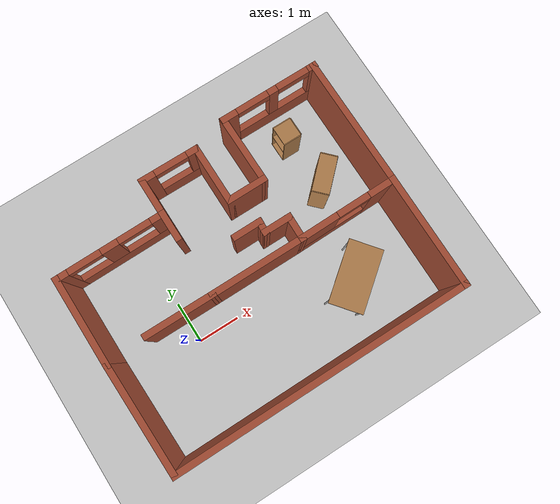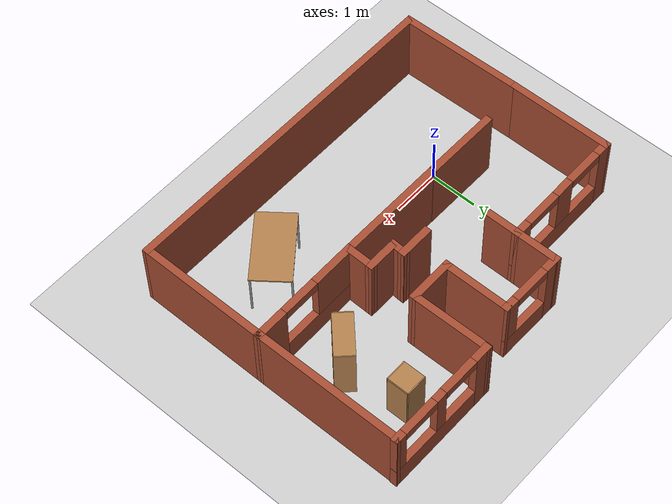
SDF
<sdf version="1.7">
 <world name="default">
  <light name="sun" type="directional">
   <pose>0 0 10 0 -0 0</pose>
   <diffuse>0.8 0.8 0.8 1</diffuse>
   <specular>0.2 0.2 0.2 1</specular>
   <attenuation>
    <range>1000</range>
    <constant>0.9</constant>
    <linear>0.01</linear>
    <quadratic>0.001</quadratic>
   </attenuation>
   <direction>-0.5 0.1 -0.9</direction>
   <spot><inner_angle>0</inner_angle><outer_angle>0</outer_angle><falloff>0</falloff></spot>
  </light>
  <model name="ground_plane">
   <static>1</static>
   <link name="link">
    <collision name="collision">
     <geometry><plane><normal>0 0 1</normal><size>100 100</size></plane></geometry>
     <surface><friction><ode><mu>100</mu><mu2>50</mu2></ode></friction></surface>
    </collision>
    <visual name="visual">
     <cast_shadows>0</cast_shadows>
     <geometry><plane><normal>0 0 1</normal><size>100 100</size></plane></geometry>
     <material>
      <script><uri>file://media/materials/scripts/gazebo.material</uri><name>Gazebo/Grey</name></script>
     </material>
    </visual>
   </link>
  </model>
  <gravity>0 0 -9.8</gravity>
  <magnetic_field>6e-06 2.3e-05 -4.2e-05</magnetic_field>
  <atmosphere type="adiabatic"/>
  <physics type="ode">
   <max_step_size>0.001</max_step_size>
   <real_time_factor>1</real_time_factor>
   <real_time_update_rate>1000</real_time_update_rate>
  </physics>
  <scene><ambient>0.4 0.4 0.4 1</ambient><background>0.7 0.7 0.7 1</background><shadows>1</shadows></scene>
  <audio><device>default</device></audio>
  <spherical_coordinates>
   <surface_model>EARTH_WGS84</surface_model>
   <latitude_deg>0</latitude_deg>
   <longitude_deg>0</longitude_deg>
   <elevation>0</elevation>
   <heading_deg>0</heading_deg>
  </spherical_coordinates>
  <model name="floorplan">
   <link name="Wall_54">
    <pose>-3.45985 0.603649 0 0 -0 0.004231</pose>
    <visual name="Wall_54_Visual_0">
     <pose>-1.19888 0 0.75 0 -0 0</pose>
     <geometry><box><size>0.35223 0.15 1.5</size></box></geometry>
     <material>
      <script><uri>file://media/materials/scripts/gazebo.material</uri><name>Gazebo/Bricks</name></script>
      <ambient>1 1 1 1</ambient>
      <shader type="pixel"/>
     </material>
     <meta><layer>0</layer></meta>
    </visual>
    <visual name="Wall_54_Visual_1">
     <pose>0.176115 0 0.25 0 -0 0</pose>
     <geometry><box><size>2.39777 0.15 0.5</size></box></geometry>
     <material>
      <script><uri>file://media/materials/scripts/gazebo.material</uri><name>Gazebo/Bricks</name></script>
      <ambient>1 1 1 1</ambient>
      <shader type="pixel"/>
     </material>
     <meta><layer>0</layer></meta>
    </visual>
    <visual name="Wall_54_Visual_2">
     <pose>-0.013166 0 1 0 -0 0</pose>
     <geometry><box><size>0.419208 0.15 1</size></box></geometry>
     <material>
      <script><uri>file://media/materials/scripts/gazebo.material</uri><name>Gazebo/Bricks</name></script>
      <ambient>1 1 1 1</ambient>
      <shader type="pixel"/>
     </material>
     <meta><layer>0</layer></meta>
    </visual>
    <visual name="Wall_54_Visual_3">
     <pose>1.18572 0 1 0 -0 0</pose>
     <geometry><box><size>0.378562 0.15 1</size></box></geometry>
     <material>
      <script><uri>file://media/materials/scripts/gazebo.material</uri><name>Gazebo/Bricks</name></script>
      <ambient>1 1 1 1</ambient>
      <shader type="pixel"/>
     </material>
     <meta><layer>0</layer></meta>
    </visual>
    <visual name="Wall_54_Visual_4">
     <pose>-0.62277 0 1.4 0 -0 0</pose>
     <geometry><box><size>0.8 0.15 0.2</size></box></geometry>
     <material>
      <script><uri>file://media/materials/scripts/gazebo.material</uri><name>Gazebo/Bricks</name></script>
      <ambient>1 1 1 1</ambient>
      <shader type="pixel"/>
     </material>
     <meta><layer>0</layer></meta>
    </visual>
    <visual name="Wall_54_Visual_5">
     <pose>0.596438 0 1.4 0 -0 0</pose>
     <geometry><box><size>0.8 0.15 0.2</size></box></geometry>
     <material>
      <script><uri>file://media/materials/scripts/gazebo.material</uri><name>Gazebo/Bricks</name></script>
      <ambient>1 1 1 1</ambient>
      <shader type="pixel"/>
     </material>
     <meta><layer>0</layer></meta>
    </visual>
    <collision name="Wall_54_Collision_0">
     <pose>-1.19888 0 0.75 0 -0 0</pose>
     <geometry><box><size>0.35223 0.15 1.5</size></box></geometry>
     <surface>
      <friction>
       <ode><mu>1</mu><mu2>1</mu2><fdir1>0 0 0</fdir1><slip1>0</slip1><slip2>0</slip2></ode>
       <torsional>
        <coefficient>1</coefficient>
        <patch_radius>0</patch_radius>
        <surface_radius>0</surface_radius>
        <use_patch_radius>1</use_patch_radius>
        <ode><slip>0</slip></ode>
       </torsional>
      </friction>
      <bounce><restitution_coefficient>0</restitution_coefficient><threshold>1e+06</threshold></bounce>
      <contact>
       <collide_without_contact>0</collide_without_contact>
       <collide_without_contact_bitmask>1</collide_without_contact_bitmask>
       <collide_bitmask>1</collide_bitmask>
       <ode>
        <soft_cfm>0</soft_cfm>
        <soft_erp>0.2</soft_erp>
        <kp>1e+13</kp>
        <kd>1</kd>
        <max_vel>0.01</max_vel>
        <min_depth>0</min_depth>
       </ode>
       <bullet>
        <split_impulse>1</split_impulse>
        <split_impulse_penetration_threshold>-0.01</split_impulse_penetration_threshold>
        <soft_cfm>0</soft_cfm>
        <soft_erp>0.2</soft_erp>
        <kp>1e+13</kp>
        <kd>1</kd>
       </bullet>
      </contact>
     </surface>
    </collision>
    <collision name="Wall_54_Collision_1">
     <pose>0.176115 0 0.25 0 -0 0</pose>
     <geometry><box><size>2.39777 0.15 0.5</size></box></geometry>
     <surface>
      <friction>
       <ode><mu>1</mu><mu2>1</mu2><fdir1>0 0 0</fdir1><slip1>0</slip1><slip2>0</slip2></ode>
       <torsional>
        <coefficient>1</coefficient>
        <patch_radius>0</patch_radius>
        <surface_radius>0</surface_radius>
        <use_patch_radius>1</use_patch_radius>
        <ode><slip>0</slip></ode>
       </torsional>
      </friction>
      <bounce><restitution_coefficient>0</restitution_coefficient><threshold>1e+06</threshold></bounce>
      <contact>
       <collide_without_contact>0</collide_without_contact>
       <collide_without_contact_bitmask>1</collide_without_contact_bitmask>
       <collide_bitmask>1</collide_bitmask>
       <ode>
        <soft_cfm>0</soft_cfm>
        <soft_erp>0.2</soft_erp>
        <kp>1e+13</kp>
        <kd>1</kd>
        <max_vel>0.01</max_vel>
        <min_depth>0</min_depth>
       </ode>
       <bullet>
        <split_impulse>1</split_impulse>
        <split_impulse_penetration_threshold>-0.01</split_impulse_penetration_threshold>
        <soft_cfm>0</soft_cfm>
        <soft_erp>0.2</soft_erp>
        <kp>1e+13</kp>
        <kd>1</kd>
       </bullet>
      </contact>
     </surface>
    </collision>
    <collision name="Wall_54_Collision_2">
     <pose>-0.013166 0 1 0 -0 0</pose>
     <geometry><box><size>0.419208 0.15 1</size></box></geometry>
     <surface>
      <friction>
       <ode><mu>1</mu><mu2>1</mu2><fdir1>0 0 0</fdir1><slip1>0</slip1><slip2>0</slip2></ode>
       <torsional>
        <coefficient>1</coefficient>
        <patch_radius>0</patch_radius>
        <surface_radius>0</surface_radius>
        <use_patch_radius>1</use_patch_radius>
        <ode><slip>0</slip></ode>
       </torsional>
      </friction>
      <bounce><restitution_coefficient>0</restitution_coefficient><threshold>1e+06</threshold></bounce>
      <contact>
       <collide_without_contact>0</collide_without_contact>
       <collide_without_contact_bitmask>1</collide_without_contact_bitmask>
       <collide_bitmask>1</collide_bitmask>
       <ode>
        <soft_cfm>0</soft_cfm>
        <soft_erp>0.2</soft_erp>
        <kp>1e+13</kp>
        <kd>1</kd>
        <max_vel>0.01</max_vel>
        <min_depth>0</min_depth>
       </ode>
       <bullet>
        <split_impulse>1</split_impulse>
        <split_impulse_penetration_threshold>-0.01</split_impulse_penetration_threshold>
        <soft_cfm>0</soft_cfm>
        <soft_erp>0.2</soft_erp>
        <kp>1e+13</kp>
        <kd>1</kd>
       </bullet>
      </contact>
     </surface>
    </collision>
    <collision name="Wall_54_Collision_3">
     <pose>1.18572 0 1 0 -0 0</pose>
     <geometry><box><size>0.378562 0.15 1</size></box></geometry>
     <surface>
      <friction>
       <ode><mu>1</mu><mu2>1</mu2><fdir1>0 0 0</fdir1><slip1>0</slip1><slip2>0</slip2></ode>
       <torsional>
        <coefficient>1</coefficient>
        <patch_radius>0</patch_radius>
        <surface_radius>0</surface_radius>
        <use_patch_radius>1</use_patch_radius>
        <ode><slip>0</slip></ode>
       </torsional>
      </friction>
      <bounce><restitution_coefficient>0</restitution_coefficient><threshold>1e+06</threshold></bounce>
      <contact>
       <collide_without_contact>0</collide_without_contact>
       <collide_without_contact_bitmask>1</collide_without_contact_bitmask>
       <collide_bitmask>1</collide_bitmask>
       <ode>
        <soft_cfm>0</soft_cfm>
        <soft_erp>0.2</soft_erp>
        <kp>1e+13</kp>
        <kd>1</kd>
        <max_vel>0.01</max_vel>
        <min_depth>0</min_depth>
       </ode>
       <bullet>
        <split_impulse>1</split_impulse>
        <split_impulse_penetration_threshold>-0.01</split_impulse_penetration_threshold>
        <soft_cfm>0</soft_cfm>
        <soft_erp>0.2</soft_erp>
        <kp>1e+13</kp>
        <kd>1</kd>
       </bullet>
      </contact>
     </surface>
    </collision>
    <collision name="Wall_54_Collision_4">
     <pose>-0.62277 0 1.4 0 -0 0</pose>
     <geometry><box><size>0.8 0.15 0.2</size></box></geometry>
     <surface>
      <friction>
       <ode><mu>1</mu><mu2>1</mu2><fdir1>0 0 0</fdir1><slip1>0</slip1><slip2>0</slip2></ode>
       <torsional>
        <coefficient>1</coefficient>
        <patch_radius>0</patch_radius>
        <surface_radius>0</surface_radius>
        <use_patch_radius>1</use_patch_radius>
        <ode><slip>0</slip></ode>
       </torsional>
      </friction>
      <bounce><restitution_coefficient>0</restitution_coefficient><threshold>1e+06</threshold></bounce>
      <contact>
       <collide_without_contact>0</collide_without_contact>
       <collide_without_contact_bitmask>1</collide_without_contact_bitmask>
       <collide_bitmask>1</collide_bitmask>
       <ode>
        <soft_cfm>0</soft_cfm>
        <soft_erp>0.2</soft_erp>
        <kp>1e+13</kp>
        <kd>1</kd>
        <max_vel>0.01</max_vel>
        <min_depth>0</min_depth>
       </ode>
       <bullet>
        <split_impulse>1</split_impulse>
        <split_impulse_penetration_threshold>-0.01</split_impulse_penetration_threshold>
        <soft_cfm>0</soft_cfm>
        <soft_erp>0.2</soft_erp>
        <kp>1e+13</kp>
        <kd>1</kd>
       </bullet>
      </contact>
     </surface>
    </collision>
    <collision name="Wall_54_Collision_5">
     <pose>0.596438 0 1.4 0 -0 0</pose>
     <geometry><box><size>0.8 0.15 0.2</size></box></geometry>
     <surface>
      <friction>
       <ode><mu>1</mu><mu2>1</mu2><fdir1>0 0 0</fdir1><slip1>0</slip1><slip2>0</slip2></ode>
       <torsional>
        <coefficient>1</coefficient>
        <patch_radius>0</patch_radius>
        <surface_radius>0</surface_radius>
        <use_patch_radius>1</use_patch_radius>
        <ode><slip>0</slip></ode>
       </torsional>
      </friction>
      <bounce><restitution_coefficient>0</restitution_coefficient><threshold>1e+06</threshold></bounce>
      <contact>
       <collide_without_contact>0</collide_without_contact>
       <collide_without_contact_bitmask>1</collide_without_contact_bitmask>
       <collide_bitmask>1</collide_bitmask>
       <ode>
        <soft_cfm>0</soft_cfm>
        <soft_erp>0.2</soft_erp>
        <kp>1e+13</kp>
        <kd>1</kd>
        <max_vel>0.01</max_vel>
        <min_depth>0</min_depth>
       </ode>
       <bullet>
        <split_impulse>1</split_impulse>
        <split_impulse_penetration_threshold>-0.01</split_impulse_penetration_threshold>
        <soft_cfm>0</soft_cfm>
        <soft_erp>0.2</soft_erp>
        <kp>1e+13</kp>
        <kd>1</kd>
       </bullet>
      </contact>
     </surface>
    </collision>
   </link>
   <link name="Wall_56">
    <pose>-2.15985 0.303649 0 0 0 -1.5708</pose>
    <visual name="Wall_56_Visual">
     <pose>0 0 0.75 0 -0 0</pose>
     <geometry><box><size>0.761 0.15 1.5</size></box></geometry>
     <material>
      <script><uri>file://media/materials/scripts/gazebo.material</uri><name>Gazebo/Bricks</name></script>
      <ambient>1 1 1 1</ambient>
      <shader type="pixel"/>
     </material>
     <meta><layer>0</layer></meta>
    </visual>
    <collision name="Wall_56_Collision">
     <pose>0 0 0.75 0 -0 0</pose>
     <geometry><box><size>0.761 0.15 1.5</size></box></geometry>
     <surface>
      <friction>
       <ode><mu>1</mu><mu2>1</mu2><fdir1>0 0 0</fdir1><slip1>0</slip1><slip2>0</slip2></ode>
       <torsional>
        <coefficient>1</coefficient>
        <patch_radius>0</patch_radius>
        <surface_radius>0</surface_radius>
        <use_patch_radius>1</use_patch_radius>
        <ode><slip>0</slip></ode>
       </torsional>
      </friction>
      <bounce><restitution_coefficient>0</restitution_coefficient><threshold>1e+06</threshold></bounce>
      <contact>
       <collide_without_contact>0</collide_without_contact>
       <collide_without_contact_bitmask>1</collide_without_contact_bitmask>
       <collide_bitmask>1</collide_bitmask>
       <ode>
        <soft_cfm>0</soft_cfm>
        <soft_erp>0.2</soft_erp>
        <kp>1e+13</kp>
        <kd>1</kd>
        <max_vel>0.01</max_vel>
        <min_depth>0</min_depth>
       </ode>
       <bullet>
        <split_impulse>1</split_impulse>
        <split_impulse_penetration_threshold>-0.01</split_impulse_penetration_threshold>
        <soft_cfm>0</soft_cfm>
        <soft_erp>0.2</soft_erp>
        <kp>1e+13</kp>
        <kd>1</kd>
       </bullet>
      </contact>
     </surface>
    </collision>
   </link>
   <link name="Wall_58">
    <pose>-2.15985 1.03465 0 0 -0 1.5708</pose>
    <visual name="Wall_58_Visual">
     <pose>0 0 0.75 0 -0 0</pose>
     <geometry><box><size>1.00024 0.15 1.5</size></box></geometry>
     <material>
      <script><uri>file://media/materials/scripts/gazebo.material</uri><name>Gazebo/Bricks</name></script>
      <ambient>1 1 1 1</ambient>
      <shader type="pixel"/>
     </material>
     <meta><layer>0</layer></meta>
    </visual>
    <collision name="Wall_58_Collision">
     <pose>0 0 0.75 0 -0 0</pose>
     <geometry><box><size>1.00024 0.15 1.5</size></box></geometry>
     <surface>
      <friction>
       <ode><mu>1</mu><mu2>1</mu2><fdir1>0 0 0</fdir1><slip1>0</slip1><slip2>0</slip2></ode>
       <torsional>
        <coefficient>1</coefficient>
        <patch_radius>0</patch_radius>
        <surface_radius>0</surface_radius>
        <use_patch_radius>1</use_patch_radius>
        <ode><slip>0</slip></ode>
       </torsional>
      </friction>
      <bounce><restitution_coefficient>0</restitution_coefficient><threshold>1e+06</threshold></bounce>
      <contact>
       <collide_without_contact>0</collide_without_contact>
       <collide_without_contact_bitmask>1</collide_without_contact_bitmask>
       <collide_bitmask>1</collide_bitmask>
       <ode>
        <soft_cfm>0</soft_cfm>
        <soft_erp>0.2</soft_erp>
        <kp>1e+13</kp>
        <kd>1</kd>
        <max_vel>0.01</max_vel>
        <min_depth>0</min_depth>
       </ode>
       <bullet>
        <split_impulse>1</split_impulse>
        <split_impulse_penetration_threshold>-0.01</split_impulse_penetration_threshold>
        <soft_cfm>0</soft_cfm>
        <soft_erp>0.2</soft_erp>
        <kp>1e+13</kp>
        <kd>1</kd>
       </bullet>
      </contact>
     </surface>
    </collision>
   </link>
   <link name="Wall_60">
    <pose>-1.48485 1.45415 0 0 0 -0.008889</pose>
    <visual name="Wall_60_Visual_0">
     <pose>-0.557435 0 0.75 0 -0 0</pose>
     <geometry><box><size>0.38513 0.15 1.5</size></box></geometry>
     <material>
      <script><uri>file://media/materials/scripts/gazebo.material</uri><name>Gazebo/Bricks</name></script>
      <ambient>1 1 1 1</ambient>
      <shader type="pixel"/>
     </material>
     <meta><layer>0</layer></meta>
    </visual>
    <visual name="Wall_60_Visual_1">
     <pose>0.192565 0 0.25 0 -0 0</pose>
     <geometry><box><size>1.11487 0.15 0.5</size></box></geometry>
     <material>
      <script><uri>file://media/materials/scripts/gazebo.material</uri><name>Gazebo/Bricks</name></script>
      <ambient>1 1 1 1</ambient>
      <shader type="pixel"/>
     </material>
     <meta><layer>0</layer></meta>
    </visual>
    <visual name="Wall_60_Visual_2">
     <pose>0.592565 0 1 0 -0 0</pose>
     <geometry><box><size>0.31487 0.15 1</size></box></geometry>
     <material>
      <script><uri>file://media/materials/scripts/gazebo.material</uri><name>Gazebo/Bricks</name></script>
      <ambient>1 1 1 1</ambient>
      <shader type="pixel"/>
     </material>
     <meta><layer>0</layer></meta>
    </visual>
    <visual name="Wall_60_Visual_3">
     <pose>0.03513 0 1.4 0 -0 0</pose>
     <geometry><box><size>0.8 0.15 0.2</size></box></geometry>
     <material>
      <script><uri>file://media/materials/scripts/gazebo.material</uri><name>Gazebo/Bricks</name></script>
      <ambient>1 1 1 1</ambient>
      <shader type="pixel"/>
     </material>
     <meta><layer>0</layer></meta>
    </visual>
    <collision name="Wall_60_Collision_0">
     <pose>-0.557435 0 0.75 0 -0 0</pose>
     <geometry><box><size>0.38513 0.15 1.5</size></box></geometry>
     <surface>
      <friction>
       <ode><mu>1</mu><mu2>1</mu2><fdir1>0 0 0</fdir1><slip1>0</slip1><slip2>0</slip2></ode>
       <torsional>
        <coefficient>1</coefficient>
        <patch_radius>0</patch_radius>
        <surface_radius>0</surface_radius>
        <use_patch_radius>1</use_patch_radius>
        <ode><slip>0</slip></ode>
       </torsional>
      </friction>
      <bounce><restitution_coefficient>0</restitution_coefficient><threshold>1e+06</threshold></bounce>
      <contact>
       <collide_without_contact>0</collide_without_contact>
       <collide_without_contact_bitmask>1</collide_without_contact_bitmask>
       <collide_bitmask>1</collide_bitmask>
       <ode>
        <soft_cfm>0</soft_cfm>
        <soft_erp>0.2</soft_erp>
        <kp>1e+13</kp>
        <kd>1</kd>
        <max_vel>0.01</max_vel>
        <min_depth>0</min_depth>
       </ode>
       <bullet>
        <split_impulse>1</split_impulse>
        <split_impulse_penetration_threshold>-0.01</split_impulse_penetration_threshold>
        <soft_cfm>0</soft_cfm>
        <soft_erp>0.2</soft_erp>
        <kp>1e+13</kp>
        <kd>1</kd>
       </bullet>
      </contact>
     </surface>
    </collision>
    <collision name="Wall_60_Collision_1">
     <pose>0.192565 0 0.25 0 -0 0</pose>
     <geometry><box><size>1.11487 0.15 0.5</size></box></geometry>
     <surface>
      <friction>
       <ode><mu>1</mu><mu2>1</mu2><fdir1>0 0 0</fdir1><slip1>0</slip1><slip2>0</slip2></ode>
       <torsional>
        <coefficient>1</coefficient>
        <patch_radius>0</patch_radius>
        <surface_radius>0</surface_radius>
        <use_patch_radius>1</use_patch_radius>
        <ode><slip>0</slip></ode>
       </torsional>
      </friction>
      <bounce><restitution_coefficient>0</restitution_coefficient><threshold>1e+06</threshold></bounce>
      <contact>
       <collide_without_contact>0</collide_without_contact>
       <collide_without_contact_bitmask>1</collide_without_contact_bitmask>
       <collide_bitmask>1</collide_bitmask>
       <ode>
        <soft_cfm>0</soft_cfm>
        <soft_erp>0.2</soft_erp>
        <kp>1e+13</kp>
        <kd>1</kd>
        <max_vel>0.01</max_vel>
        <min_depth>0</min_depth>
       </ode>
       <bullet>
        <split_impulse>1</split_impulse>
        <split_impulse_penetration_threshold>-0.01</split_impulse_penetration_threshold>
        <soft_cfm>0</soft_cfm>
        <soft_erp>0.2</soft_erp>
        <kp>1e+13</kp>
        <kd>1</kd>
       </bullet>
      </contact>
     </surface>
    </collision>
    <collision name="Wall_60_Collision_3">
     <pose>0.03513 0 1.4 0 -0 0</pose>
     <geometry><box><size>0.8 0.15 0.2</size></box></geometry>
     <surface>
      <friction>
       <ode><mu>1</mu><mu2>1</mu2><fdir1>0 0 0</fdir1><slip1>0</slip1><slip2>0</slip2></ode>
       <torsional>
        <coefficient>1</coefficient>
        <patch_radius>0</patch_radius>
        <surface_radius>0</surface_radius>
        <use_patch_radius>1</use_patch_radius>
        <ode><slip>0</slip></ode>
       </torsional>
      </friction>
      <bounce><restitution_coefficient>0</restitution_coefficient><threshold>1e+06</threshold></bounce>
      <contact>
       <collide_without_contact>0</collide_without_contact>
       <collide_without_contact_bitmask>1</collide_without_contact_bitmask>
       <collide_bitmask>1</collide_bitmask>
       <ode>
        <soft_cfm>0</soft_cfm>
        <soft_erp>0.2</soft_erp>
        <kp>1e+13</kp>
        <kd>1</kd>
        <max_vel>0.01</max_vel>
        <min_depth>0</min_depth>
       </ode>
       <bullet>
        <split_impulse>1</split_impulse>
        <split_impulse_penetration_threshold>-0.01</split_impulse_penetration_threshold>
        <soft_cfm>0</soft_cfm>
        <soft_erp>0.2</soft_erp>
        <kp>1e+13</kp>
        <kd>1</kd>
       </bullet>
      </contact>
     </surface>
    </collision>
    <collision name="Wall_60_Collision_2">
     <pose>0.592565 0 1 0 -0 0</pose>
     <geometry><box><size>0.31487 0.15 1</size></box></geometry>
     <surface>
      <friction>
       <ode><mu>1</mu><mu2>1</mu2><fdir1>0 0 0</fdir1><slip1>0</slip1><slip2>0</slip2></ode>
       <torsional>
        <coefficient>1</coefficient>
        <patch_radius>0</patch_radius>
        <surface_radius>0</surface_radius>
        <use_patch_radius>1</use_patch_radius>
        <ode><slip>0</slip></ode>
       </torsional>
      </friction>
      <bounce><restitution_coefficient>0</restitution_coefficient><threshold>1e+06</threshold></bounce>
      <contact>
       <collide_without_contact>0</collide_without_contact>
       <collide_without_contact_bitmask>1</collide_without_contact_bitmask>
       <collide_bitmask>1</collide_bitmask>
       <ode>
        <soft_cfm>0</soft_cfm>
        <soft_erp>0.2</soft_erp>
        <kp>1e+13</kp>
        <kd>1</kd>
        <max_vel>0.01</max_vel>
        <min_depth>0</min_depth>
       </ode>
       <bullet>
        <split_impulse>1</split_impulse>
        <split_impulse_penetration_threshold>-0.01</split_impulse_penetration_threshold>
        <soft_cfm>0</soft_cfm>
        <soft_erp>0.2</soft_erp>
        <kp>1e+13</kp>
        <kd>1</kd>
       </bullet>
      </contact>
     </surface>
    </collision>
   </link>
   <link name="Wall_61">
    <pose>-0.809851 0.773149 0 0 0 -1.5708</pose>
    <visual name="Wall_61_Visual">
     <pose>0 0 0.75 0 -0 0</pose>
     <geometry><box><size>1.5 0.15 1.5</size></box></geometry>
     <material>
      <script><uri>file://media/materials/scripts/gazebo.material</uri><name>Gazebo/Bricks</name></script>
      <ambient>1 1 1 1</ambient>
      <shader type="pixel"/>
     </material>
     <meta><layer>0</layer></meta>
    </visual>
    <collision name="Wall_61_Collision">
     <pose>0 0 0.75 0 -0 0</pose>
     <geometry><box><size>1.5 0.15 1.5</size></box></geometry>
     <surface>
      <friction>
       <ode><mu>1</mu><mu2>1</mu2><fdir1>0 0 0</fdir1><slip1>0</slip1><slip2>0</slip2></ode>
       <torsional>
        <coefficient>1</coefficient>
        <patch_radius>0</patch_radius>
        <surface_radius>0</surface_radius>
        <use_patch_radius>1</use_patch_radius>
        <ode><slip>0</slip></ode>
       </torsional>
      </friction>
      <bounce><restitution_coefficient>0</restitution_coefficient><threshold>1e+06</threshold></bounce>
      <contact>
       <collide_without_contact>0</collide_without_contact>
       <collide_without_contact_bitmask>1</collide_without_contact_bitmask>
       <collide_bitmask>1</collide_bitmask>
       <ode>
        <soft_cfm>0</soft_cfm>
        <soft_erp>0.2</soft_erp>
        <kp>1e+13</kp>
        <kd>1</kd>
        <max_vel>0.01</max_vel>
        <min_depth>0</min_depth>
       </ode>
       <bullet>
        <split_impulse>1</split_impulse>
        <split_impulse_penetration_threshold>-0.01</split_impulse_penetration_threshold>
        <soft_cfm>0</soft_cfm>
        <soft_erp>0.2</soft_erp>
        <kp>1e+13</kp>
        <kd>1</kd>
       </bullet>
      </contact>
     </surface>
    </collision>
   </link>
   <link name="Wall_62">
    <pose>-0.379351 0.098149 0 0 -0 0</pose>
    <visual name="Wall_62_Visual">
     <pose>0 0 0.75 0 -0 0</pose>
     <geometry><box><size>1.011 0.15 1.5</size></box></geometry>
     <material>
      <script><uri>file://media/materials/scripts/gazebo.material</uri><name>Gazebo/Bricks</name></script>
      <ambient>1 1 1 1</ambient>
      <shader type="pixel"/>
     </material>
     <meta><layer>0</layer></meta>
    </visual>
    <collision name="Wall_62_Collision">
     <pose>0 0 0.75 0 -0 0</pose>
     <geometry><box><size>1.011 0.15 1.5</size></box></geometry>
     <surface>
      <friction>
       <ode><mu>1</mu><mu2>1</mu2><fdir1>0 0 0</fdir1><slip1>0</slip1><slip2>0</slip2></ode>
       <torsional>
        <coefficient>1</coefficient>
        <patch_radius>0</patch_radius>
        <surface_radius>0</surface_radius>
        <use_patch_radius>1</use_patch_radius>
        <ode><slip>0</slip></ode>
       </torsional>
      </friction>
      <bounce><restitution_coefficient>0</restitution_coefficient><threshold>1e+06</threshold></bounce>
      <contact>
       <collide_without_contact>0</collide_without_contact>
       <collide_without_contact_bitmask>1</collide_without_contact_bitmask>
       <collide_bitmask>1</collide_bitmask>
       <ode>
        <soft_cfm>0</soft_cfm>
        <soft_erp>0.2</soft_erp>
        <kp>1e+13</kp>
        <kd>1</kd>
        <max_vel>0.01</max_vel>
        <min_depth>0</min_depth>
       </ode>
       <bullet>
        <split_impulse>1</split_impulse>
        <split_impulse_penetration_threshold>-0.01</split_impulse_penetration_threshold>
        <soft_cfm>0</soft_cfm>
        <soft_erp>0.2</soft_erp>
        <kp>1e+13</kp>
        <kd>1</kd>
       </bullet>
      </contact>
     </surface>
    </collision>
   </link>
   <link name="Wall_63">
    <pose>0.045164 0.891664 0 0 -0 1.57834</pose>
    <visual name="Wall_63_Visual">
     <pose>0 0 0.75 0 -0 0</pose>
     <geometry><box><size>1.73707 0.15 1.5</size></box></geometry>
     <material>
      <script><uri>file://media/materials/scripts/gazebo.material</uri><name>Gazebo/Bricks</name></script>
      <ambient>1 1 1 1</ambient>
      <shader type="pixel"/>
     </material>
     <meta><layer>0</layer></meta>
    </visual>
    <collision name="Wall_63_Collision">
     <pose>0 0 0.75 0 -0 0</pose>
     <geometry><box><size>1.73707 0.15 1.5</size></box></geometry>
     <surface>
      <friction>
       <ode><mu>1</mu><mu2>1</mu2><fdir1>0 0 0</fdir1><slip1>0</slip1><slip2>0</slip2></ode>
       <torsional>
        <coefficient>1</coefficient>
        <patch_radius>0</patch_radius>
        <surface_radius>0</surface_radius>
        <use_patch_radius>1</use_patch_radius>
        <ode><slip>0</slip></ode>
       </torsional>
      </friction>
      <bounce><restitution_coefficient>0</restitution_coefficient><threshold>1e+06</threshold></bounce>
      <contact>
       <collide_without_contact>0</collide_without_contact>
       <collide_without_contact_bitmask>1</collide_without_contact_bitmask>
       <collide_bitmask>1</collide_bitmask>
       <ode>
        <soft_cfm>0</soft_cfm>
        <soft_erp>0.2</soft_erp>
        <kp>1e+13</kp>
        <kd>1</kd>
        <max_vel>0.01</max_vel>
        <min_depth>0</min_depth>
       </ode>
       <bullet>
        <split_impulse>1</split_impulse>
        <split_impulse_penetration_threshold>-0.01</split_impulse_penetration_threshold>
        <soft_cfm>0</soft_cfm>
        <soft_erp>0.2</soft_erp>
        <kp>1e+13</kp>
        <kd>1</kd>
       </bullet>
      </contact>
     </surface>
    </collision>
   </link>
   <link name="Wall_64">
    <pose>1.22115 1.68518 0 0 -0 0</pose>
    <visual name="Wall_64_Visual_0">
     <pose>-1.042 0 0.75 0 -0 0</pose>
     <geometry><box><size>0.404011 0.15 1.5</size></box></geometry>
     <material>
      <script><uri>file://media/materials/scripts/gazebo.material</uri><name>Gazebo/Bricks</name></script>
      <ambient>1 1 1 1</ambient>
      <shader type="pixel"/>
     </material>
     <meta><layer>0</layer></meta>
    </visual>
    <visual name="Wall_64_Visual_1">
     <pose>0.202005 0 0.25 0 -0 0</pose>
     <geometry><box><size>2.08399 0.15 0.5</size></box></geometry>
     <material>
      <script><uri>file://media/materials/scripts/gazebo.material</uri><name>Gazebo/Bricks</name></script>
      <ambient>1 1 1 1</ambient>
      <shader type="pixel"/>
     </material>
     <meta><layer>0</layer></meta>
    </visual>
    <visual name="Wall_64_Visual_2">
     <pose>0.078804 0 1 0 -0 0</pose>
     <geometry><box><size>0.237586 0.15 1</size></box></geometry>
     <material>
      <script><uri>file://media/materials/scripts/gazebo.material</uri><name>Gazebo/Bricks</name></script>
      <ambient>1 1 1 1</ambient>
      <shader type="pixel"/>
     </material>
     <meta><layer>0</layer></meta>
    </visual>
    <visual name="Wall_64_Visual_3">
     <pose>1.1208 0 1 0 -0 0</pose>
     <geometry><box><size>0.246403 0.15 1</size></box></geometry>
     <material>
      <script><uri>file://media/materials/scripts/gazebo.material</uri><name>Gazebo/Bricks</name></script>
      <ambient>1 1 1 1</ambient>
      <shader type="pixel"/>
     </material>
     <meta><layer>0</layer></meta>
    </visual>
    <visual name="Wall_64_Visual_4">
     <pose>-0.439989 0 1.4 0 -0 0</pose>
     <geometry><box><size>0.8 0.15 0.2</size></box></geometry>
     <material>
      <script><uri>file://media/materials/scripts/gazebo.material</uri><name>Gazebo/Bricks</name></script>
      <ambient>1 1 1 1</ambient>
      <shader type="pixel"/>
     </material>
     <meta><layer>0</layer></meta>
    </visual>
    <visual name="Wall_64_Visual_5">
     <pose>0.597597 0 1.4 0 -0 0</pose>
     <geometry><box><size>0.8 0.15 0.2</size></box></geometry>
     <material>
      <script><uri>file://media/materials/scripts/gazebo.material</uri><name>Gazebo/Bricks</name></script>
      <ambient>1 1 1 1</ambient>
      <shader type="pixel"/>
     </material>
     <meta><layer>0</layer></meta>
    </visual>
    <collision name="Wall_64_Collision_0">
     <pose>-1.042 0 0.75 0 -0 0</pose>
     <geometry><box><size>0.404011 0.15 1.5</size></box></geometry>
     <surface>
      <friction>
       <ode><mu>1</mu><mu2>1</mu2><fdir1>0 0 0</fdir1><slip1>0</slip1><slip2>0</slip2></ode>
       <torsional>
        <coefficient>1</coefficient>
        <patch_radius>0</patch_radius>
        <surface_radius>0</surface_radius>
        <use_patch_radius>1</use_patch_radius>
        <ode><slip>0</slip></ode>
       </torsional>
      </friction>
      <bounce><restitution_coefficient>0</restitution_coefficient><threshold>1e+06</threshold></bounce>
      <contact>
       <collide_without_contact>0</collide_without_contact>
       <collide_without_contact_bitmask>1</collide_without_contact_bitmask>
       <collide_bitmask>1</collide_bitmask>
       <ode>
        <soft_cfm>0</soft_cfm>
        <soft_erp>0.2</soft_erp>
        <kp>1e+13</kp>
        <kd>1</kd>
        <max_vel>0.01</max_vel>
        <min_depth>0</min_depth>
       </ode>
       <bullet>
        <split_impulse>1</split_impulse>
        <split_impulse_penetration_threshold>-0.01</split_impulse_penetration_threshold>
        <soft_cfm>0</soft_cfm>
        <soft_erp>0.2</soft_erp>
        <kp>1e+13</kp>
        <kd>1</kd>
       </bullet>
      </contact>
     </surface>
    </collision>
    <collision name="Wall_64_Collision_1">
     <pose>0.202005 0 0.25 0 -0 0</pose>
     <geometry><box><size>2.08399 0.15 0.5</size></box></geometry>
     <surface>
      <friction>
       <ode><mu>1</mu><mu2>1</mu2><fdir1>0 0 0</fdir1><slip1>0</slip1><slip2>0</slip2></ode>
       <torsional>
        <coefficient>1</coefficient>
        <patch_radius>0</patch_radius>
        <surface_radius>0</surface_radius>
        <use_patch_radius>1</use_patch_radius>
        <ode><slip>0</slip></ode>
       </torsional>
      </friction>
      <bounce><restitution_coefficient>0</restitution_coefficient><threshold>1e+06</threshold></bounce>
      <contact>
       <collide_without_contact>0</collide_without_contact>
       <collide_without_contact_bitmask>1</collide_without_contact_bitmask>
       <collide_bitmask>1</collide_bitmask>
       <ode>
        <soft_cfm>0</soft_cfm>
        <soft_erp>0.2</soft_erp>
        <kp>1e+13</kp>
        <kd>1</kd>
        <max_vel>0.01</max_vel>
        <min_depth>0</min_depth>
       </ode>
       <bullet>
        <split_impulse>1</split_impulse>
        <split_impulse_penetration_threshold>-0.01</split_impulse_penetration_threshold>
        <soft_cfm>0</soft_cfm>
        <soft_erp>0.2</soft_erp>
        <kp>1e+13</kp>
        <kd>1</kd>
       </bullet>
      </contact>
     </surface>
    </collision>
    <collision name="Wall_64_Collision_2">
     <pose>0.078804 0 1 0 -0 0</pose>
     <geometry><box><size>0.237586 0.15 1</size></box></geometry>
     <surface>
      <friction>
       <ode><mu>1</mu><mu2>1</mu2><fdir1>0 0 0</fdir1><slip1>0</slip1><slip2>0</slip2></ode>
       <torsional>
        <coefficient>1</coefficient>
        <patch_radius>0</patch_radius>
        <surface_radius>0</surface_radius>
        <use_patch_radius>1</use_patch_radius>
        <ode><slip>0</slip></ode>
       </torsional>
      </friction>
      <bounce><restitution_coefficient>0</restitution_coefficient><threshold>1e+06</threshold></bounce>
      <contact>
       <collide_without_contact>0</collide_without_contact>
       <collide_without_contact_bitmask>1</collide_without_contact_bitmask>
       <collide_bitmask>1</collide_bitmask>
       <ode>
        <soft_cfm>0</soft_cfm>
        <soft_erp>0.2</soft_erp>
        <kp>1e+13</kp>
        <kd>1</kd>
        <max_vel>0.01</max_vel>
        <min_depth>0</min_depth>
       </ode>
       <bullet>
        <split_impulse>1</split_impulse>
        <split_impulse_penetration_threshold>-0.01</split_impulse_penetration_threshold>
        <soft_cfm>0</soft_cfm>
        <soft_erp>0.2</soft_erp>
        <kp>1e+13</kp>
        <kd>1</kd>
       </bullet>
      </contact>
     </surface>
    </collision>
    <collision name="Wall_64_Collision_3">
     <pose>1.1208 0 1 0 -0 0</pose>
     <geometry><box><size>0.246403 0.15 1</size></box></geometry>
     <surface>
      <friction>
       <ode><mu>1</mu><mu2>1</mu2><fdir1>0 0 0</fdir1><slip1>0</slip1><slip2>0</slip2></ode>
       <torsional>
        <coefficient>1</coefficient>
        <patch_radius>0</patch_radius>
        <surface_radius>0</surface_radius>
        <use_patch_radius>1</use_patch_radius>
        <ode><slip>0</slip></ode>
       </torsional>
      </friction>
      <bounce><restitution_coefficient>0</restitution_coefficient><threshold>1e+06</threshold></bounce>
      <contact>
       <collide_without_contact>0</collide_without_contact>
       <collide_without_contact_bitmask>1</collide_without_contact_bitmask>
       <collide_bitmask>1</collide_bitmask>
       <ode>
        <soft_cfm>0</soft_cfm>
        <soft_erp>0.2</soft_erp>
        <kp>1e+13</kp>
        <kd>1</kd>
        <max_vel>0.01</max_vel>
        <min_depth>0</min_depth>
       </ode>
       <bullet>
        <split_impulse>1</split_impulse>
        <split_impulse_penetration_threshold>-0.01</split_impulse_penetration_threshold>
        <soft_cfm>0</soft_cfm>
        <soft_erp>0.2</soft_erp>
        <kp>1e+13</kp>
        <kd>1</kd>
       </bullet>
      </contact>
     </surface>
    </collision>
    <collision name="Wall_64_Collision_4">
     <pose>-0.439989 0 1.4 0 -0 0</pose>
     <geometry><box><size>0.8 0.15 0.2</size></box></geometry>
     <surface>
      <friction>
       <ode><mu>1</mu><mu2>1</mu2><fdir1>0 0 0</fdir1><slip1>0</slip1><slip2>0</slip2></ode>
       <torsional>
        <coefficient>1</coefficient>
        <patch_radius>0</patch_radius>
        <surface_radius>0</surface_radius>
        <use_patch_radius>1</use_patch_radius>
        <ode><slip>0</slip></ode>
       </torsional>
      </friction>
      <bounce><restitution_coefficient>0</restitution_coefficient><threshold>1e+06</threshold></bounce>
      <contact>
       <collide_without_contact>0</collide_without_contact>
       <collide_without_contact_bitmask>1</collide_without_contact_bitmask>
       <collide_bitmask>1</collide_bitmask>
       <ode>
        <soft_cfm>0</soft_cfm>
        <soft_erp>0.2</soft_erp>
        <kp>1e+13</kp>
        <kd>1</kd>
        <max_vel>0.01</max_vel>
        <min_depth>0</min_depth>
       </ode>
       <bullet>
        <split_impulse>1</split_impulse>
        <split_impulse_penetration_threshold>-0.01</split_impulse_penetration_threshold>
        <soft_cfm>0</soft_cfm>
        <soft_erp>0.2</soft_erp>
        <kp>1e+13</kp>
        <kd>1</kd>
       </bullet>
      </contact>
     </surface>
    </collision>
    <collision name="Wall_64_Collision_5">
     <pose>0.597597 0 1.4 0 -0 0</pose>
     <geometry><box><size>0.8 0.15 0.2</size></box></geometry>
     <surface>
      <friction>
       <ode><mu>1</mu><mu2>1</mu2><fdir1>0 0 0</fdir1><slip1>0</slip1><slip2>0</slip2></ode>
       <torsional>
        <coefficient>1</coefficient>
        <patch_radius>0</patch_radius>
        <surface_radius>0</surface_radius>
        <use_patch_radius>1</use_patch_radius>
        <ode><slip>0</slip></ode>
       </torsional>
      </friction>
      <bounce><restitution_coefficient>0</restitution_coefficient><threshold>1e+06</threshold></bounce>
      <contact>
       <collide_without_contact>0</collide_without_contact>
       <collide_without_contact_bitmask>1</collide_without_contact_bitmask>
       <collide_bitmask>1</collide_bitmask>
       <ode>
        <soft_cfm>0</soft_cfm>
        <soft_erp>0.2</soft_erp>
        <kp>1e+13</kp>
        <kd>1</kd>
        <max_vel>0.01</max_vel>
        <min_depth>0</min_depth>
       </ode>
       <bullet>
        <split_impulse>1</split_impulse>
        <split_impulse_penetration_threshold>-0.01</split_impulse_penetration_threshold>
        <soft_cfm>0</soft_cfm>
        <soft_erp>0.2</soft_erp>
        <kp>1e+13</kp>
        <kd>1</kd>
       </bullet>
      </contact>
     </surface>
    </collision>
   </link>
   <link name="Wall_65">
    <pose>2.38366 0.141664 0 0 0 -1.56659</pose>
    <visual name="Wall_65_Visual">
     <pose>0 0 0.75 0 -0 0</pose>
     <geometry><box><size>3.23706 0.15 1.5</size></box></geometry>
     <material>
      <script><uri>file://media/materials/scripts/gazebo.material</uri><name>Gazebo/Bricks</name></script>
      <ambient>1 1 1 1</ambient>
      <shader type="pixel"/>
     </material>
     <meta><layer>0</layer></meta>
    </visual>
    <collision name="Wall_65_Collision">
     <pose>0 0 0.75 0 -0 0</pose>
     <geometry><box><size>3.23706 0.15 1.5</size></box></geometry>
     <surface>
      <friction>
       <ode><mu>1</mu><mu2>1</mu2><fdir1>0 0 0</fdir1><slip1>0</slip1><slip2>0</slip2></ode>
       <torsional>
        <coefficient>1</coefficient>
        <patch_radius>0</patch_radius>
        <surface_radius>0</surface_radius>
        <use_patch_radius>1</use_patch_radius>
        <ode><slip>0</slip></ode>
       </torsional>
      </friction>
      <bounce><restitution_coefficient>0</restitution_coefficient><threshold>1e+06</threshold></bounce>
      <contact>
       <collide_without_contact>0</collide_without_contact>
       <collide_without_contact_bitmask>1</collide_without_contact_bitmask>
       <collide_bitmask>1</collide_bitmask>
       <ode>
        <soft_cfm>0</soft_cfm>
        <soft_erp>0.2</soft_erp>
        <kp>1e+13</kp>
        <kd>1</kd>
        <max_vel>0.01</max_vel>
        <min_depth>0</min_depth>
       </ode>
       <bullet>
        <split_impulse>1</split_impulse>
        <split_impulse_penetration_threshold>-0.01</split_impulse_penetration_threshold>
        <soft_cfm>0</soft_cfm>
        <soft_erp>0.2</soft_erp>
        <kp>1e+13</kp>
        <kd>1</kd>
       </bullet>
      </contact>
     </surface>
    </collision>
   </link>
   <link name="Wall_66">
    <pose>1.22115 -1.41335 0 0 0 -3.13176</pose>
    <visual name="Wall_66_Visual_0">
     <pose>-0.893824 0 0.75 0 -0 0</pose>
     <geometry><box><size>0.700692 0.15 1.5</size></box></geometry>
     <material>
      <script><uri>file://media/materials/scripts/gazebo.material</uri><name>Gazebo/Bricks</name></script>
      <ambient>1 1 1 1</ambient>
      <shader type="pixel"/>
     </material>
     <meta><layer>0</layer></meta>
    </visual>
    <visual name="Wall_66_Visual_1">
     <pose>0.350346 0 0.25 0 -0 0</pose>
     <geometry><box><size>1.78765 0.15 0.5</size></box></geometry>
     <material>
      <script><uri>file://media/materials/scripts/gazebo.material</uri><name>Gazebo/Bricks</name></script>
      <ambient>1 1 1 1</ambient>
      <shader type="pixel"/>
     </material>
     <meta><layer>0</layer></meta>
    </visual>
    <visual name="Wall_66_Visual_2">
     <pose>0.750346 0 1 0 -0 0</pose>
     <geometry><box><size>0.987649 0.15 1</size></box></geometry>
     <material>
      <script><uri>file://media/materials/scripts/gazebo.material</uri><name>Gazebo/Bricks</name></script>
      <ambient>1 1 1 1</ambient>
      <shader type="pixel"/>
     </material>
     <meta><layer>0</layer></meta>
    </visual>
    <visual name="Wall_66_Visual_3">
     <pose>-0.143478 0 1.4 0 -0 0</pose>
     <geometry><box><size>0.8 0.15 0.2</size></box></geometry>
     <material>
      <script><uri>file://media/materials/scripts/gazebo.material</uri><name>Gazebo/Bricks</name></script>
      <ambient>1 1 1 1</ambient>
      <shader type="pixel"/>
     </material>
     <meta><layer>0</layer></meta>
    </visual>
    <collision name="Wall_66_Collision_0">
     <pose>-0.893824 0 0.75 0 -0 0</pose>
     <geometry><box><size>0.700692 0.15 1.5</size></box></geometry>
     <surface>
      <friction>
       <ode><mu>1</mu><mu2>1</mu2><fdir1>0 0 0</fdir1><slip1>0</slip1><slip2>0</slip2></ode>
       <torsional>
        <coefficient>1</coefficient>
        <patch_radius>0</patch_radius>
        <surface_radius>0</surface_radius>
        <use_patch_radius>1</use_patch_radius>
        <ode><slip>0</slip></ode>
       </torsional>
      </friction>
      <bounce><restitution_coefficient>0</restitution_coefficient><threshold>1e+06</threshold></bounce>
      <contact>
       <collide_without_contact>0</collide_without_contact>
       <collide_without_contact_bitmask>1</collide_without_contact_bitmask>
       <collide_bitmask>1</collide_bitmask>
       <ode>
        <soft_cfm>0</soft_cfm>
        <soft_erp>0.2</soft_erp>
        <kp>1e+13</kp>
        <kd>1</kd>
        <max_vel>0.01</max_vel>
        <min_depth>0</min_depth>
       </ode>
       <bullet>
        <split_impulse>1</split_impulse>
        <split_impulse_penetration_threshold>-0.01</split_impulse_penetration_threshold>
        <soft_cfm>0</soft_cfm>
        <soft_erp>0.2</soft_erp>
        <kp>1e+13</kp>
        <kd>1</kd>
       </bullet>
      </contact>
     </surface>
    </collision>
    <collision name="Wall_66_Collision_1">
     <pose>0.350346 0 0.25 0 -0 0</pose>
     <geometry><box><size>1.78765 0.15 0.5</size></box></geometry>
     <surface>
      <friction>
       <ode><mu>1</mu><mu2>1</mu2><fdir1>0 0 0</fdir1><slip1>0</slip1><slip2>0</slip2></ode>
       <torsional>
        <coefficient>1</coefficient>
        <patch_radius>0</patch_radius>
        <surface_radius>0</surface_radius>
        <use_patch_radius>1</use_patch_radius>
        <ode><slip>0</slip></ode>
       </torsional>
      </friction>
      <bounce><restitution_coefficient>0</restitution_coefficient><threshold>1e+06</threshold></bounce>
      <contact>
       <collide_without_contact>0</collide_without_contact>
       <collide_without_contact_bitmask>1</collide_without_contact_bitmask>
       <collide_bitmask>1</collide_bitmask>
       <ode>
        <soft_cfm>0</soft_cfm>
        <soft_erp>0.2</soft_erp>
        <kp>1e+13</kp>
        <kd>1</kd>
        <max_vel>0.01</max_vel>
        <min_depth>0</min_depth>
       </ode>
       <bullet>
        <split_impulse>1</split_impulse>
        <split_impulse_penetration_threshold>-0.01</split_impulse_penetration_threshold>
        <soft_cfm>0</soft_cfm>
        <soft_erp>0.2</soft_erp>
        <kp>1e+13</kp>
        <kd>1</kd>
       </bullet>
      </contact>
     </surface>
    </collision>
    <collision name="Wall_66_Collision_2">
     <pose>0.750346 0 1 0 -0 0</pose>
     <geometry><box><size>0.987649 0.15 1</size></box></geometry>
     <surface>
      <friction>
       <ode><mu>1</mu><mu2>1</mu2><fdir1>0 0 0</fdir1><slip1>0</slip1><slip2>0</slip2></ode>
       <torsional>
        <coefficient>1</coefficient>
        <patch_radius>0</patch_radius>
        <surface_radius>0</surface_radius>
        <use_patch_radius>1</use_patch_radius>
        <ode><slip>0</slip></ode>
       </torsional>
      </friction>
      <bounce><restitution_coefficient>0</restitution_coefficient><threshold>1e+06</threshold></bounce>
      <contact>
       <collide_without_contact>0</collide_without_contact>
       <collide_without_contact_bitmask>1</collide_without_contact_bitmask>
       <collide_bitmask>1</collide_bitmask>
       <ode>
        <soft_cfm>0</soft_cfm>
        <soft_erp>0.2</soft_erp>
        <kp>1e+13</kp>
        <kd>1</kd>
        <max_vel>0.01</max_vel>
        <min_depth>0</min_depth>
       </ode>
       <bullet>
        <split_impulse>1</split_impulse>
        <split_impulse_penetration_threshold>-0.01</split_impulse_penetration_threshold>
        <soft_cfm>0</soft_cfm>
        <soft_erp>0.2</soft_erp>
        <kp>1e+13</kp>
        <kd>1</kd>
       </bullet>
      </contact>
     </surface>
    </collision>
    <collision name="Wall_66_Collision_3">
     <pose>-0.143478 0 1.4 0 -0 0</pose>
     <geometry><box><size>0.8 0.15 0.2</size></box></geometry>
     <surface>
      <friction>
       <ode><mu>1</mu><mu2>1</mu2><fdir1>0 0 0</fdir1><slip1>0</slip1><slip2>0</slip2></ode>
       <torsional>
        <coefficient>1</coefficient>
        <patch_radius>0</patch_radius>
        <surface_radius>0</surface_radius>
        <use_patch_radius>1</use_patch_radius>
        <ode><slip>0</slip></ode>
       </torsional>
      </friction>
      <bounce><restitution_coefficient>0</restitution_coefficient><threshold>1e+06</threshold></bounce>
      <contact>
       <collide_without_contact>0</collide_without_contact>
       <collide_without_contact_bitmask>1</collide_without_contact_bitmask>
       <collide_bitmask>1</collide_bitmask>
       <ode>
        <soft_cfm>0</soft_cfm>
        <soft_erp>0.2</soft_erp>
        <kp>1e+13</kp>
        <kd>1</kd>
        <max_vel>0.01</max_vel>
        <min_depth>0</min_depth>
       </ode>
       <bullet>
        <split_impulse>1</split_impulse>
        <split_impulse_penetration_threshold>-0.01</split_impulse_penetration_threshold>
        <soft_cfm>0</soft_cfm>
        <soft_erp>0.2</soft_erp>
        <kp>1e+13</kp>
        <kd>1</kd>
       </bullet>
      </contact>
     </surface>
    </collision>
   </link>
   <link name="Wall_67">
    <pose>0.057649 -1.15935 0 0 -0 1.55008</pose>
    <visual name="Wall_67_Visual">
     <pose>0 0 0.75 0 -0 0</pose>
     <geometry><box><size>0.681545 0.15 1.5</size></box></geometry>
     <material>
      <script><uri>file://media/materials/scripts/gazebo.material</uri><name>Gazebo/Bricks</name></script>
      <ambient>1 1 1 1</ambient>
      <shader type="pixel"/>
     </material>
     <meta><layer>0</layer></meta>
    </visual>
    <collision name="Wall_67_Collision">
     <pose>0 0 0.75 0 -0 0</pose>
     <geometry><box><size>0.681545 0.15 1.5</size></box></geometry>
     <surface>
      <friction>
       <ode><mu>1</mu><mu2>1</mu2><fdir1>0 0 0</fdir1><slip1>0</slip1><slip2>0</slip2></ode>
       <torsional>
        <coefficient>1</coefficient>
        <patch_radius>0</patch_radius>
        <surface_radius>0</surface_radius>
        <use_patch_radius>1</use_patch_radius>
        <ode><slip>0</slip></ode>
       </torsional>
      </friction>
      <bounce><restitution_coefficient>0</restitution_coefficient><threshold>1e+06</threshold></bounce>
      <contact>
       <collide_without_contact>0</collide_without_contact>
       <collide_without_contact_bitmask>1</collide_without_contact_bitmask>
       <collide_bitmask>1</collide_bitmask>
       <ode>
        <soft_cfm>0</soft_cfm>
        <soft_erp>0.2</soft_erp>
        <kp>1e+13</kp>
        <kd>1</kd>
        <max_vel>0.01</max_vel>
        <min_depth>0</min_depth>
       </ode>
       <bullet>
        <split_impulse>1</split_impulse>
        <split_impulse_penetration_threshold>-0.01</split_impulse_penetration_threshold>
        <soft_cfm>0</soft_cfm>
        <soft_erp>0.2</soft_erp>
        <kp>1e+13</kp>
        <kd>1</kd>
       </bullet>
      </contact>
     </surface>
    </collision>
   </link>
   <link name="Wall_69">
    <pose>-0.236851 -0.893851 0 0 -0 3.14159</pose>
    <visual name="Wall_69_Visual">
     <pose>0 0 0.75 0 -0 0</pose>
     <geometry><box><size>0.75 0.15 1.5</size></box></geometry>
     <material>
      <script><uri>file://media/materials/scripts/gazebo.material</uri><name>Gazebo/Bricks</name></script>
      <ambient>1 1 1 1</ambient>
      <shader type="pixel"/>
     </material>
     <meta><layer>0</layer></meta>
    </visual>
    <collision name="Wall_69_Collision">
     <pose>0 0 0.75 0 -0 0</pose>
     <geometry><box><size>0.75 0.15 1.5</size></box></geometry>
     <surface>
      <friction>
       <ode><mu>1</mu><mu2>1</mu2><fdir1>0 0 0</fdir1><slip1>0</slip1><slip2>0</slip2></ode>
       <torsional>
        <coefficient>1</coefficient>
        <patch_radius>0</patch_radius>
        <surface_radius>0</surface_radius>
        <use_patch_radius>1</use_patch_radius>
        <ode><slip>0</slip></ode>
       </torsional>
      </friction>
      <bounce><restitution_coefficient>0</restitution_coefficient><threshold>1e+06</threshold></bounce>
      <contact>
       <collide_without_contact>0</collide_without_contact>
       <collide_without_contact_bitmask>1</collide_without_contact_bitmask>
       <collide_bitmask>1</collide_bitmask>
       <ode>
        <soft_cfm>0</soft_cfm>
        <soft_erp>0.2</soft_erp>
        <kp>1e+13</kp>
        <kd>1</kd>
        <max_vel>0.01</max_vel>
        <min_depth>0</min_depth>
       </ode>
       <bullet>
        <split_impulse>1</split_impulse>
        <split_impulse_penetration_threshold>-0.01</split_impulse_penetration_threshold>
        <soft_cfm>0</soft_cfm>
        <soft_erp>0.2</soft_erp>
        <kp>1e+13</kp>
        <kd>1</kd>
       </bullet>
      </contact>
     </surface>
    </collision>
   </link>
   <link name="Wall_70">
    <pose>-0.529351 -0.768351 0 0 -0 1.51111</pose>
    <visual name="Wall_70_Visual">
     <pose>0 0 0.75 0 -0 0</pose>
     <geometry><box><size>0.40097 0.15 1.5</size></box></geometry>
     <material>
      <script><uri>file://media/materials/scripts/gazebo.material</uri><name>Gazebo/Bricks</name></script>
      <ambient>1 1 1 1</ambient>
      <shader type="pixel"/>
     </material>
     <meta><layer>0</layer></meta>
    </visual>
    <collision name="Wall_70_Collision">
     <pose>0 0 0.75 0 -0 0</pose>
     <geometry><box><size>0.40097 0.15 1.5</size></box></geometry>
     <surface>
      <friction>
       <ode><mu>1</mu><mu2>1</mu2><fdir1>0 0 0</fdir1><slip1>0</slip1><slip2>0</slip2></ode>
       <torsional>
        <coefficient>1</coefficient>
        <patch_radius>0</patch_radius>
        <surface_radius>0</surface_radius>
        <use_patch_radius>1</use_patch_radius>
        <ode><slip>0</slip></ode>
       </torsional>
      </friction>
      <bounce><restitution_coefficient>0</restitution_coefficient><threshold>1e+06</threshold></bounce>
      <contact>
       <collide_without_contact>0</collide_without_contact>
       <collide_without_contact_bitmask>1</collide_without_contact_bitmask>
       <collide_bitmask>1</collide_bitmask>
       <ode>
        <soft_cfm>0</soft_cfm>
        <soft_erp>0.2</soft_erp>
        <kp>1e+13</kp>
        <kd>1</kd>
        <max_vel>0.01</max_vel>
        <min_depth>0</min_depth>
       </ode>
       <bullet>
        <split_impulse>1</split_impulse>
        <split_impulse_penetration_threshold>-0.01</split_impulse_penetration_threshold>
        <soft_cfm>0</soft_cfm>
        <soft_erp>0.2</soft_erp>
        <kp>1e+13</kp>
        <kd>1</kd>
       </bullet>
      </contact>
     </surface>
    </collision>
   </link>
   <link name="Wall_71">
    <pose>-0.821851 -0.642851 0 0 -0 3.14159</pose>
    <visual name="Wall_71_Visual">
     <pose>0 0 0.75 0 -0 0</pose>
     <geometry><box><size>0.75 0.15 1.5</size></box></geometry>
     <material>
      <script><uri>file://media/materials/scripts/gazebo.material</uri><name>Gazebo/Bricks</name></script>
      <ambient>1 1 1 1</ambient>
      <shader type="pixel"/>
     </material>
     <meta><layer>0</layer></meta>
    </visual>
    <collision name="Wall_71_Collision">
     <pose>0 0 0.75 0 -0 0</pose>
     <geometry><box><size>0.75 0.15 1.5</size></box></geometry>
     <surface>
      <friction>
       <ode><mu>1</mu><mu2>1</mu2><fdir1>0 0 0</fdir1><slip1>0</slip1><slip2>0</slip2></ode>
       <torsional>
        <coefficient>1</coefficient>
        <patch_radius>0</patch_radius>
        <surface_radius>0</surface_radius>
        <use_patch_radius>1</use_patch_radius>
        <ode><slip>0</slip></ode>
       </torsional>
      </friction>
      <bounce><restitution_coefficient>0</restitution_coefficient><threshold>1e+06</threshold></bounce>
      <contact>
       <collide_without_contact>0</collide_without_contact>
       <collide_without_contact_bitmask>1</collide_without_contact_bitmask>
       <collide_bitmask>1</collide_bitmask>
       <ode>
        <soft_cfm>0</soft_cfm>
        <soft_erp>0.2</soft_erp>
        <kp>1e+13</kp>
        <kd>1</kd>
        <max_vel>0.01</max_vel>
        <min_depth>0</min_depth>
       </ode>
       <bullet>
        <split_impulse>1</split_impulse>
        <split_impulse_penetration_threshold>-0.01</split_impulse_penetration_threshold>
        <soft_cfm>0</soft_cfm>
        <soft_erp>0.2</soft_erp>
        <kp>1e+13</kp>
        <kd>1</kd>
       </bullet>
      </contact>
     </surface>
    </collision>
   </link>
   <link name="Wall_74">
    <pose>-1.05885 -1.42135 0 0 0 -0.00315</pose>
    <visual name="Wall_74_Visual">
     <pose>0 0 0.75 0 -0 0</pose>
     <geometry><box><size>2.37213 0.15 1.5</size></box></geometry>
     <material>
      <script><uri>file://media/materials/scripts/gazebo.material</uri><name>Gazebo/Bricks</name></script>
      <ambient>1 1 1 1</ambient>
      <shader type="pixel"/>
     </material>
     <meta><layer>0</layer></meta>
    </visual>
    <collision name="Wall_74_Collision">
     <pose>0 0 0.75 0 -0 0</pose>
     <geometry><box><size>2.37213 0.15 1.5</size></box></geometry>
     <surface>
      <friction>
       <ode><mu>1</mu><mu2>1</mu2><fdir1>0 0 0</fdir1><slip1>0</slip1><slip2>0</slip2></ode>
       <torsional>
        <coefficient>1</coefficient>
        <patch_radius>0</patch_radius>
        <surface_radius>0</surface_radius>
        <use_patch_radius>1</use_patch_radius>
        <ode><slip>0</slip></ode>
       </torsional>
      </friction>
      <bounce><restitution_coefficient>0</restitution_coefficient><threshold>1e+06</threshold></bounce>
      <contact>
       <collide_without_contact>0</collide_without_contact>
       <collide_without_contact_bitmask>1</collide_without_contact_bitmask>
       <collide_bitmask>1</collide_bitmask>
       <ode>
        <soft_cfm>0</soft_cfm>
        <soft_erp>0.2</soft_erp>
        <kp>1e+13</kp>
        <kd>1</kd>
        <max_vel>0.01</max_vel>
        <min_depth>0</min_depth>
       </ode>
       <bullet>
        <split_impulse>1</split_impulse>
        <split_impulse_penetration_threshold>-0.01</split_impulse_penetration_threshold>
        <soft_cfm>0</soft_cfm>
        <soft_erp>0.2</soft_erp>
        <kp>1e+13</kp>
        <kd>1</kd>
       </bullet>
      </contact>
     </surface>
    </collision>
   </link>
   <link name="Wall_77">
    <pose>-2.97585 -1.41235 0 0 -0 3.13477</pose>
    <visual name="Wall_77_Visual">
     <pose>0 0 0.75 0 -0 0</pose>
     <geometry><box><size>1.76193 0.15 1.5</size></box></geometry>
     <material>
      <script><uri>file://media/materials/scripts/gazebo.material</uri><name>Gazebo/Bricks</name></script>
      <ambient>1 1 1 1</ambient>
      <shader type="pixel"/>
     </material>
     <meta><layer>0</layer></meta>
    </visual>
    <collision name="Wall_77_Collision">
     <pose>0 0 0.75 0 -0 0</pose>
     <geometry><box><size>1.76193 0.15 1.5</size></box></geometry>
     <surface>
      <friction>
       <ode><mu>1</mu><mu2>1</mu2><fdir1>0 0 0</fdir1><slip1>0</slip1><slip2>0</slip2></ode>
       <torsional>
        <coefficient>1</coefficient>
        <patch_radius>0</patch_radius>
        <surface_radius>0</surface_radius>
        <use_patch_radius>1</use_patch_radius>
        <ode><slip>0</slip></ode>
       </torsional>
      </friction>
      <bounce><restitution_coefficient>0</restitution_coefficient><threshold>1e+06</threshold></bounce>
      <contact>
       <collide_without_contact>0</collide_without_contact>
       <collide_without_contact_bitmask>1</collide_without_contact_bitmask>
       <collide_bitmask>1</collide_bitmask>
       <ode>
        <soft_cfm>0</soft_cfm>
        <soft_erp>0.2</soft_erp>
        <kp>1e+13</kp>
        <kd>1</kd>
        <max_vel>0.01</max_vel>
        <min_depth>0</min_depth>
       </ode>
       <bullet>
        <split_impulse>1</split_impulse>
        <split_impulse_penetration_threshold>-0.01</split_impulse_penetration_threshold>
        <soft_cfm>0</soft_cfm>
        <soft_erp>0.2</soft_erp>
        <kp>1e+13</kp>
        <kd>1</kd>
       </bullet>
      </contact>
     </surface>
    </collision>
   </link>
   <link name="Wall_79">
    <pose>-4.75985 -0.451851 0 0 0 -1.5708</pose>
    <visual name="Wall_79_Visual">
     <pose>0 0 0.75 0 -0 0</pose>
     <geometry><box><size>2.25 0.15 1.5</size></box></geometry>
     <material>
      <script><uri>file://media/materials/scripts/gazebo.material</uri><name>Gazebo/Bricks</name></script>
      <ambient>1 1 1 1</ambient>
      <shader type="pixel"/>
     </material>
     <meta><layer>0</layer></meta>
    </visual>
    <collision name="Wall_79_Collision">
     <pose>0 0 0.75 0 -0 0</pose>
     <geometry><box><size>2.25 0.15 1.5</size></box></geometry>
     <surface>
      <friction>
       <ode><mu>1</mu><mu2>1</mu2><fdir1>0 0 0</fdir1><slip1>0</slip1><slip2>0</slip2></ode>
       <torsional>
        <coefficient>1</coefficient>
        <patch_radius>0</patch_radius>
        <surface_radius>0</surface_radius>
        <use_patch_radius>1</use_patch_radius>
        <ode><slip>0</slip></ode>
       </torsional>
      </friction>
      <bounce><restitution_coefficient>0</restitution_coefficient><threshold>1e+06</threshold></bounce>
      <contact>
       <collide_without_contact>0</collide_without_contact>
       <collide_without_contact_bitmask>1</collide_without_contact_bitmask>
       <collide_bitmask>1</collide_bitmask>
       <ode>
        <soft_cfm>0</soft_cfm>
        <soft_erp>0.2</soft_erp>
        <kp>1e+13</kp>
        <kd>1</kd>
        <max_vel>0.01</max_vel>
        <min_depth>0</min_depth>
       </ode>
       <bullet>
        <split_impulse>1</split_impulse>
        <split_impulse_penetration_threshold>-0.01</split_impulse_penetration_threshold>
        <soft_cfm>0</soft_cfm>
        <soft_erp>0.2</soft_erp>
        <kp>1e+13</kp>
        <kd>1</kd>
       </bullet>
      </contact>
     </surface>
    </collision>
   </link>
   <link name="Wall_81">
    <pose>-4.73735 -2.79035 0 0 0 -1.55334</pose>
    <visual name="Wall_81_Visual">
     <pose>0 0 0.75 0 -0 0</pose>
     <geometry><box><size>2.72739 0.15 1.5</size></box></geometry>
     <material>
      <script><uri>file://media/materials/scripts/gazebo.material</uri><name>Gazebo/Bricks</name></script>
      <ambient>1 1 1 1</ambient>
      <shader type="pixel"/>
     </material>
     <meta><layer>0</layer></meta>
    </visual>
    <collision name="Wall_81_Collision">
     <pose>0 0 0.75 0 -0 0</pose>
     <geometry><box><size>2.72739 0.15 1.5</size></box></geometry>
     <surface>
      <friction>
       <ode><mu>1</mu><mu2>1</mu2><fdir1>0 0 0</fdir1><slip1>0</slip1><slip2>0</slip2></ode>
       <torsional>
        <coefficient>1</coefficient>
        <patch_radius>0</patch_radius>
        <surface_radius>0</surface_radius>
        <use_patch_radius>1</use_patch_radius>
        <ode><slip>0</slip></ode>
       </torsional>
      </friction>
      <bounce><restitution_coefficient>0</restitution_coefficient><threshold>1e+06</threshold></bounce>
      <contact>
       <collide_without_contact>0</collide_without_contact>
       <collide_without_contact_bitmask>1</collide_without_contact_bitmask>
       <collide_bitmask>1</collide_bitmask>
       <ode>
        <soft_cfm>0</soft_cfm>
        <soft_erp>0.2</soft_erp>
        <kp>1e+13</kp>
        <kd>1</kd>
        <max_vel>0.01</max_vel>
        <min_depth>0</min_depth>
       </ode>
       <bullet>
        <split_impulse>1</split_impulse>
        <split_impulse_penetration_threshold>-0.01</split_impulse_penetration_threshold>
        <soft_cfm>0</soft_cfm>
        <soft_erp>0.2</soft_erp>
        <kp>1e+13</kp>
        <kd>1</kd>
       </bullet>
      </contact>
     </surface>
    </collision>
   </link>
   <link name="Wall_82">
    <pose>-1.16485 -4.07885 0 0 -0 0</pose>
    <visual name="Wall_82_Visual">
     <pose>0 0 0.75 0 -0 0</pose>
     <geometry><box><size>7.25 0.15 1.5</size></box></geometry>
     <material>
      <script><uri>file://media/materials/scripts/gazebo.material</uri><name>Gazebo/Bricks</name></script>
      <ambient>1 1 1 1</ambient>
      <shader type="pixel"/>
     </material>
     <meta><layer>0</layer></meta>
    </visual>
    <collision name="Wall_82_Collision">
     <pose>0 0 0.75 0 -0 0</pose>
     <geometry><box><size>7.25 0.15 1.5</size></box></geometry>
     <surface>
      <friction>
       <ode><mu>1</mu><mu2>1</mu2><fdir1>0 0 0</fdir1><slip1>0</slip1><slip2>0</slip2></ode>
       <torsional>
        <coefficient>1</coefficient>
        <patch_radius>0</patch_radius>
        <surface_radius>0</surface_radius>
        <use_patch_radius>1</use_patch_radius>
        <ode><slip>0</slip></ode>
       </torsional>
      </friction>
      <bounce><restitution_coefficient>0</restitution_coefficient><threshold>1e+06</threshold></bounce>
      <contact>
       <collide_without_contact>0</collide_without_contact>
       <collide_without_contact_bitmask>1</collide_without_contact_bitmask>
       <collide_bitmask>1</collide_bitmask>
       <ode>
        <soft_cfm>0</soft_cfm>
        <soft_erp>0.2</soft_erp>
        <kp>1e+13</kp>
        <kd>1</kd>
        <max_vel>0.01</max_vel>
        <min_depth>0</min_depth>
       </ode>
       <bullet>
        <split_impulse>1</split_impulse>
        <split_impulse_penetration_threshold>-0.01</split_impulse_penetration_threshold>
        <soft_cfm>0</soft_cfm>
        <soft_erp>0.2</soft_erp>
        <kp>1e+13</kp>
        <kd>1</kd>
       </bullet>
      </contact>
     </surface>
    </collision>
   </link>
   <link name="Wall_83">
    <pose>2.38765 -2.74035 0 0 -0 1.56893</pose>
    <visual name="Wall_83_Visual">
     <pose>0 0 0.75 0 -0 0</pose>
     <geometry><box><size>2.82701 0.15 1.5</size></box></geometry>
     <material>
      <script><uri>file://media/materials/scripts/gazebo.material</uri><name>Gazebo/Bricks</name></script>
      <ambient>1 1 1 1</ambient>
      <shader type="pixel"/>
     </material>
     <meta><layer>0</layer></meta>
    </visual>
    <collision name="Wall_83_Collision">
     <pose>0 0 0.75 0 -0 0</pose>
     <geometry><box><size>2.82701 0.15 1.5</size></box></geometry>
     <surface>
      <friction>
       <ode><mu>1</mu><mu2>1</mu2><fdir1>0 0 0</fdir1><slip1>0</slip1><slip2>0</slip2></ode>
       <torsional>
        <coefficient>1</coefficient>
        <patch_radius>0</patch_radius>
        <surface_radius>0</surface_radius>
        <use_patch_radius>1</use_patch_radius>
        <ode><slip>0</slip></ode>
       </torsional>
      </friction>
      <bounce><restitution_coefficient>0</restitution_coefficient><threshold>1e+06</threshold></bounce>
      <contact>
       <collide_without_contact>0</collide_without_contact>
       <collide_without_contact_bitmask>1</collide_without_contact_bitmask>
       <collide_bitmask>1</collide_bitmask>
       <ode>
        <soft_cfm>0</soft_cfm>
        <soft_erp>0.2</soft_erp>
        <kp>1e+13</kp>
        <kd>1</kd>
        <max_vel>0.01</max_vel>
        <min_depth>0</min_depth>
       </ode>
       <bullet>
        <split_impulse>1</split_impulse>
        <split_impulse_penetration_threshold>-0.01</split_impulse_penetration_threshold>
        <soft_cfm>0</soft_cfm>
        <soft_erp>0.2</soft_erp>
        <kp>1e+13</kp>
        <kd>1</kd>
       </bullet>
      </contact>
     </surface>
    </collision>
   </link>
   <static>1</static>
   <pose>3 2 0 0 -0 0</pose>
  </model>
  <model name="bookshelf">
   <static>1</static>
   <link name="link">
    <inertial><mass>1</mass></inertial>
    <collision name="back">
     <pose>0 0.005 0.6 0 -0 0</pose>
     <geometry><box><size>0.9 0.01 1.2</size></box></geometry>
    </collision>
    <visual name="visual1">
     <pose>0 0.005 0.6 0 -0 0</pose>
     <geometry><box><size>0.9 0.01 1.2</size></box></geometry>
     <material>
      <script><uri>file://media/materials/scripts/gazebo.material</uri><name>Gazebo/Wood</name></script>
     </material>
    </visual>
    <collision name="left_side">
     <pose>0.45 -0.195 0.6 0 -0 0</pose>
     <geometry><box><size>0.02 0.4 1.2</size></box></geometry>
    </collision>
    <visual name="visual2">
     <pose>0.45 -0.195 0.6 0 -0 0</pose>
     <geometry><box><size>0.02 0.4 1.2</size></box></geometry>
     <material>
      <script><uri>file://media/materials/scripts/gazebo.material</uri><name>Gazebo/Wood</name></script>
     </material>
    </visual>
    <collision name="right_side">
     <pose>-0.45 -0.195 0.6 0 -0 0</pose>
     <geometry><box><size>0.02 0.4 1.2</size></box></geometry>
    </collision>
    <visual name="visual3">
     <pose>-0.45 -0.195 0.6 0 -0 0</pose>
     <geometry><box><size>0.02 0.4 1.2</size></box></geometry>
     <material>
      <script><uri>file://media/materials/scripts/gazebo.material</uri><name>Gazebo/Wood</name></script>
     </material>
    </visual>
    <collision name="bottom">
     <pose>0 -0.195 0.03 0 -0 0</pose>
     <geometry><box><size>0.88 0.4 0.06</size></box></geometry>
    </collision>
    <visual name="visual4">
     <pose>0 -0.195 0.03 0 -0 0</pose>
     <geometry><box><size>0.88 0.4 0.06</size></box></geometry>
     <material>
      <script><uri>file://media/materials/scripts/gazebo.material</uri><name>Gazebo/Wood</name></script>
     </material>
    </visual>
    <collision name="top">
     <pose>0 -0.195 1.19 0 -0 0</pose>
     <geometry><box><size>0.88 0.4 0.02</size></box></geometry>
    </collision>
    <visual name="visual5">
     <pose>0 -0.195 1.19 0 -0 0</pose>
     <geometry><box><size>0.88 0.4 0.02</size></box></geometry>
     <material>
      <script><uri>file://media/materials/scripts/gazebo.material</uri><name>Gazebo/Wood</name></script>
     </material>
    </visual>
    <collision name="low_shelf">
     <pose>0 -0.195 0.43 0 -0 0</pose>
     <geometry><box><size>0.88 0.4 0.02</size></box></geometry>
    </collision>
    <visual name="visual6">
     <pose>0 -0.195 0.43 0 -0 0</pose>
     <geometry><box><size>0.88 0.4 0.02</size></box></geometry>
     <material>
      <script><uri>file://media/materials/scripts/gazebo.material</uri><name>Gazebo/Wood</name></script>
     </material>
    </visual>
    <collision name="high_shelf">
     <pose>0 -0.195 0.8 0 -0 0</pose>
     <geometry><box><size>0.88 0.4 0.02</size></box></geometry>
    </collision>
    <visual name="visual7">
     <pose>0 -0.195 0.8 0 -0 0</pose>
     <geometry><box><size>0.88 0.4 0.02</size></box></geometry>
     <material>
      <script><uri>file://media/materials/scripts/gazebo.material</uri><name>Gazebo/Wood</name></script>
     </material>
    </visual>
   </link>
   <pose>4.44159 1.41114 0 0 0 -2.37471</pose>
  </model>
  <model name="cabinet">
   <static>1</static>
   <link name="cabinet_bottom_plate">
    <inertial>
     <pose>0 0 -1 0 -0 0</pose>
     <inertia><ixx>2.05</ixx><ixy>0</ixy><ixz>0</ixz><iyy>2.05</iyy><iyz>0</iyz><izz>2.05</izz></inertia>
     <mass>25</mass>
    </inertial>
    <collision name="cabinet_bottom_plate_geom">
     <pose>0 0 0.01 0 -0 0</pose>
     <geometry><box><size>0.45 0.45 0.02</size></box></geometry>
    </collision>
    <visual name="cabinet_bottom_plate_geom_visual">
     <pose>0 0 0.01 0 -0 0</pose>
     <geometry><box><size>0.45 0.45 0.02</size></box></geometry>
     <material>
      <script><uri>file://media/materials/scripts/gazebo.material</uri><name>Gazebo/Wood</name></script>
     </material>
    </visual>
    <collision name="cabinet_bottom_plate_geom_cabinet_back_plate">
     <pose>0.235 0 0.51 0 -0 0</pose>
     <geometry><box><size>0.02 0.45 1.02</size></box></geometry>
    </collision>
    <visual name="cabinet_bottom_plate_geom_cabinet_back_plate_visual">
     <pose>0.235 0 0.51 0 -0 0</pose>
     <geometry><box><size>0.02 0.45 1.02</size></box></geometry>
     <material>
      <script><uri>file://media/materials/scripts/gazebo.material</uri><name>Gazebo/Wood</name></script>
     </material>
    </visual>
    <collision name="cabinet_bottom_plate_geom_cabinet_left_plate">
     <pose>0 0.235 0.51 0 -0 0</pose>
     <geometry><box><size>0.45 0.02 1.02</size></box></geometry>
    </collision>
    <visual name="cabinet_bottom_plate_geom_cabinet_left_plate_visual">
     <pose>0 0.235 0.51 0 -0 0</pose>
     <geometry><box><size>0.45 0.02 1.02</size></box></geometry>
     <material>
      <script><uri>file://media/materials/scripts/gazebo.material</uri><name>Gazebo/Wood</name></script>
     </material>
    </visual>
    <collision name="cabinet_bottom_plate_geom_cabinet_middle_plate">
     <pose>0 0 0.51 0 -0 0</pose>
     <geometry><box><size>0.45 0.45 0.02</size></box></geometry>
    </collision>
    <visual name="cabinet_bottom_plate_geom_cabinet_middle_plate_visual">
     <pose>0 0 0.51 0 -0 0</pose>
     <geometry><box><size>0.45 0.45 0.02</size></box></geometry>
     <material>
      <script><uri>file://media/materials/scripts/gazebo.material</uri><name>Gazebo/Wood</name></script>
     </material>
    </visual>
    <collision name="cabinet_bottom_plate_geom_cabinet_right_plate">
     <pose>0 -0.235 0.51 0 -0 0</pose>
     <geometry><box><size>0.45 0.02 1.02</size></box></geometry>
    </collision>
    <visual name="cabinet_bottom_plate_geom_cabinet_right_plate_visual">
     <pose>0 -0.235 0.51 0 -0 0</pose>
     <geometry><box><size>0.45 0.02 1.02</size></box></geometry>
     <material>
      <script><uri>file://media/materials/scripts/gazebo.material</uri><name>Gazebo/Wood</name></script>
     </material>
    </visual>
    <collision name="cabinet_bottom_plate_geom_cabinet_top_plate">
     <pose>0 0 1.01 0 -0 0</pose>
     <geometry><box><size>0.45 0.45 0.02</size></box></geometry>
    </collision>
    <visual name="cabinet_bottom_plate_geom_cabinet_top_plate_visual">
     <pose>0 0 1.01 0 -0 0</pose>
     <geometry><box><size>0.45 0.45 0.02</size></box></geometry>
     <material>
      <script><uri>file://media/materials/scripts/gazebo.material</uri><name>Gazebo/Wood</name></script>
     </material>
    </visual>
   </link>
   <pose>4.17812 2.86795 0 0 -0 0</pose>
  </model>
  <model name="table">
   <static>1</static>
   <link name="link">
    <collision name="surface">
     <pose>0 0 1 0 -0 0</pose>
     <geometry><box><size>1.5 0.8 0.03</size></box></geometry>
     <surface><friction><ode><mu>0.6</mu><mu2>0.6</mu2></ode></friction></surface>
    </collision>
    <visual name="visual1">
     <pose>0 0 1 0 -0 0</pose>
     <geometry><box><size>1.5 0.8 0.03</size></box></geometry>
     <material>
      <script><uri>file://media/materials/scripts/gazebo.material</uri><name>Gazebo/Wood</name></script>
     </material>
    </visual>
    <collision name="front_left_leg">
     <pose>0.68 0.38 0.5 0 -0 0</pose>
     <geometry><cylinder><radius>0.02</radius><length>1</length></cylinder></geometry>
    </collision>
    <visual name="front_left_leg">
     <pose>0.68 0.38 0.5 0 -0 0</pose>
     <geometry><cylinder><radius>0.02</radius><length>1</length></cylinder></geometry>
     <material>
      <script><uri>file://media/materials/scripts/gazebo.material</uri><name>Gazebo/Grey</name></script>
     </material>
    </visual>
    <collision name="front_right_leg">
     <pose>0.68 -0.38 0.5 0 -0 0</pose>
     <geometry><cylinder><radius>0.02</radius><length>1</length></cylinder></geometry>
    </collision>
    <visual name="front_right_leg">
     <pose>0.68 -0.38 0.5 0 -0 0</pose>
     <geometry><cylinder><radius>0.02</radius><length>1</length></cylinder></geometry>
     <material>
      <script><uri>file://media/materials/scripts/gazebo.material</uri><name>Gazebo/Grey</name></script>
     </material>
    </visual>
    <collision name="back_right_leg">
     <pose>-0.68 -0.38 0.5 0 -0 0</pose>
     <geometry><cylinder><radius>0.02</radius><length>1</length></cylinder></geometry>
    </collision>
    <visual name="back_right_leg">
     <pose>-0.68 -0.38 0.5 0 -0 0</pose>
     <geometry><cylinder><radius>0.02</radius><length>1</length></cylinder></geometry>
     <material>
      <script><uri>file://media/materials/scripts/gazebo.material</uri><name>Gazebo/Grey</name></script>
     </material>
    </visual>
    <collision name="back_left_leg">
     <pose>-0.68 0.38 0.5 0 -0 0</pose>
     <geometry><cylinder><radius>0.02</radius><length>1</length></cylinder></geometry>
    </collision>
    <visual name="back_left_leg">
     <pose>-0.68 0.38 0.5 0 -0 0</pose>
     <geometry><cylinder><radius>0.02</radius><length>1</length></cylinder></geometry>
     <material>
      <script><uri>file://media/materials/scripts/gazebo.material</uri><name>Gazebo/Grey</name></script>
     </material>
    </visual>
   </link>
   <pose>3.65554 -0.702786 0 0 -0 0.669435</pose>
  </model>
 </world>
</sdf>
